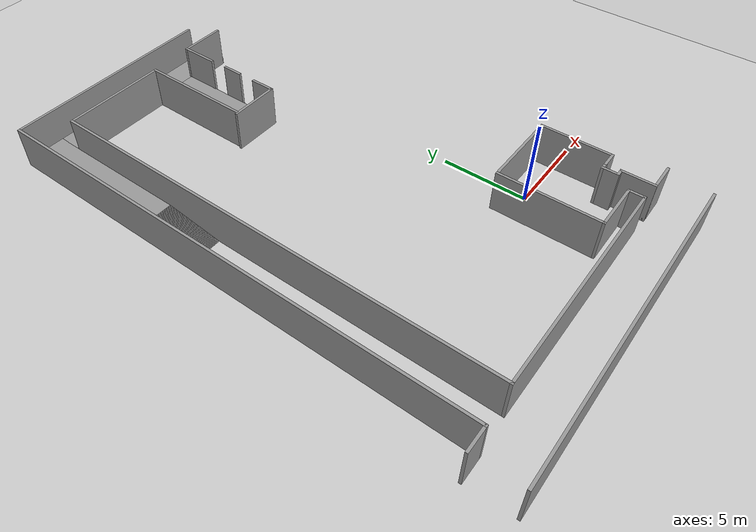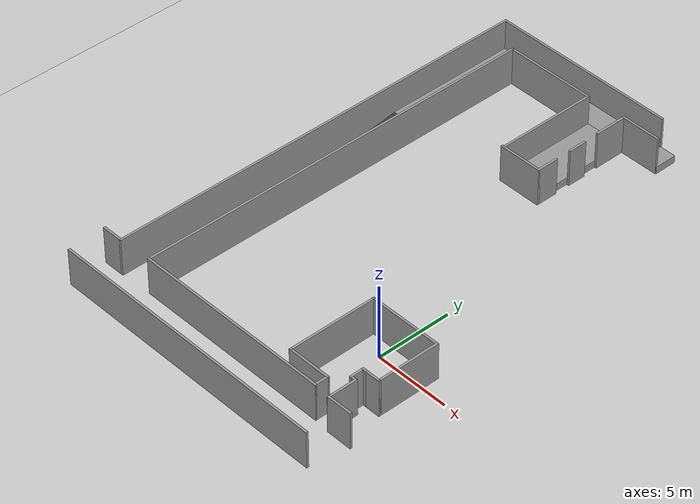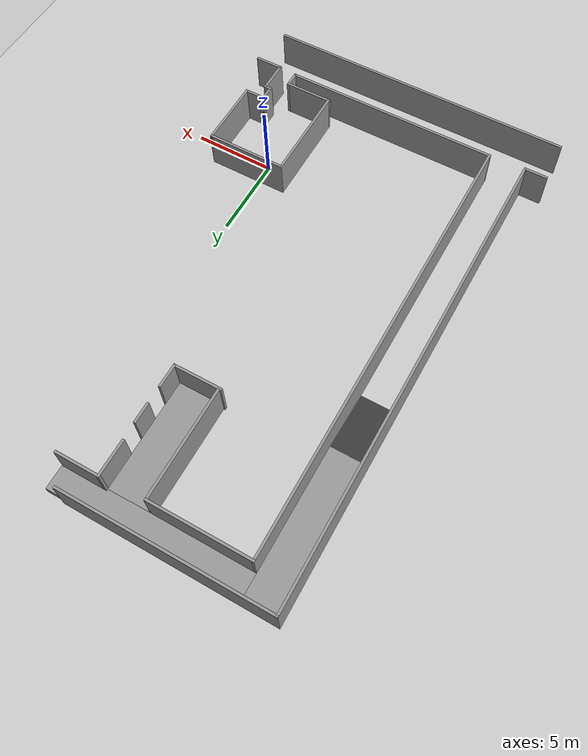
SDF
<sdf version="1.6">
 <world name="default">
  <light name="sun" type="directional">
   <pose>0 0 10 0 -0 0</pose>
   <diffuse>0.8 0.8 0.8 1</diffuse>
   <specular>0.1 0.1 0.1 1</specular>
   <attenuation>
    <range>1000</range>
    <constant>0.9</constant>
    <linear>0.01</linear>
    <quadratic>0.001</quadratic>
   </attenuation>
   <direction>-0.5 0.5 -1</direction>
  </light>
  <model name="ground_plane">
   <static>1</static>
   <link name="link">
    <collision name="collision">
     <geometry><plane><normal>0 0 1</normal><size>100 100</size></plane></geometry>
     <surface><friction><ode><mu>100</mu><mu2>50</mu2></ode></friction></surface>
    </collision>
    <visual name="visual">
     <cast_shadows>0</cast_shadows>
     <geometry><plane><normal>0 0 1</normal><size>100 100</size></plane></geometry>
     <material>
      <script><uri>file://media/materials/scripts/gazebo.material</uri><name>Gazebo/Grey</name></script>
     </material>
    </visual>
   </link>
  </model>
  <gravity>0 0 -9.8</gravity>
  <magnetic_field>6e-06 2.3e-05 -4.2e-05</magnetic_field>
  <atmosphere type="adiabatic"/>
  <physics name="default_physics" default="0" type="ode">
   <max_step_size>0.001</max_step_size>
   <real_time_factor>1</real_time_factor>
   <real_time_update_rate>1000</real_time_update_rate>
  </physics>
  <scene><ambient>0.4 0.4 0.4 1</ambient><background>0.7 0.7 0.7 1</background><shadows>1</shadows></scene>
  <spherical_coordinates>
   <surface_model>EARTH_WGS84</surface_model>
   <latitude_deg>0</latitude_deg>
   <longitude_deg>0</longitude_deg>
   <elevation>0</elevation>
   <heading_deg>0</heading_deg>
  </spherical_coordinates>
  <model name="HRI_MAP">
   <pose>-5.86756 7.56266 0 0 -0 0</pose>
   <link name="Stairs_10">
    <visual name="Stairs_10_Visual_0">
     <pose>1.21481 10.9204 0.25 0 -0 0</pose>
     <geometry><box><size>2.592 6.736 0.5</size></box></geometry>
     <material>
      <script><uri>file://media/materials/scripts/gazebo.material</uri><name>Gazebo/Grey</name></script>
      <ambient>1 1 1 1</ambient>
     </material>
    </visual>
    <collision name="Stairs_10_Collision_0">
     <geometry><box><size>2.592 6.736 0.5</size></box></geometry>
     <pose>1.21481 10.9204 0.25 0 -0 0</pose>
    </collision>
   </link>
   <link name="Stairs_2">
    <visual name="Stairs_2_Visual_0">
     <pose>-7.39374 3.33186 0.0025 0 -0 -3.14159</pose>
     <geometry><box><size>2.14498 0.035 0.005</size></box></geometry>
     <material>
      <script><uri>file://media/materials/scripts/gazebo.material</uri><name>Gazebo/Grey</name></script>
      <ambient>1 1 1 1</ambient>
     </material>
    </visual>
    <collision name="Stairs_2_Collision_0">
     <geometry><box><size>2.14498 0.035 0.005</size></box></geometry>
     <pose>-7.39374 3.33186 0.0025 0 -0 -3.14159</pose>
    </collision>
    <visual name="Stairs_2_Visual_1">
     <pose>-7.39374 3.36686 0.0075 0 -0 -3.14159</pose>
     <geometry><box><size>2.14498 0.035 0.005</size></box></geometry>
     <material>
      <script><uri>file://media/materials/scripts/gazebo.material</uri><name>Gazebo/Grey</name></script>
      <ambient>1 1 1 1</ambient>
     </material>
    </visual>
    <collision name="Stairs_2_Collision_1">
     <geometry><box><size>2.14498 0.035 0.005</size></box></geometry>
     <pose>-7.39374 3.36686 0.0075 0 -0 -3.14159</pose>
    </collision>
    <visual name="Stairs_2_Visual_2">
     <pose>-7.39374 3.40186 0.0125 0 -0 -3.14159</pose>
     <geometry><box><size>2.14498 0.035 0.005</size></box></geometry>
     <material>
      <script><uri>file://media/materials/scripts/gazebo.material</uri><name>Gazebo/Grey</name></script>
      <ambient>1 1 1 1</ambient>
     </material>
    </visual>
    <collision name="Stairs_2_Collision_2">
     <geometry><box><size>2.14498 0.035 0.005</size></box></geometry>
     <pose>-7.39374 3.40186 0.0125 0 -0 -3.14159</pose>
    </collision>
    <visual name="Stairs_2_Visual_3">
     <pose>-7.39374 3.43686 0.0175 0 -0 -3.14159</pose>
     <geometry><box><size>2.14498 0.035 0.005</size></box></geometry>
     <material>
      <script><uri>file://media/materials/scripts/gazebo.material</uri><name>Gazebo/Grey</name></script>
      <ambient>1 1 1 1</ambient>
     </material>
    </visual>
    <collision name="Stairs_2_Collision_3">
     <geometry><box><size>2.14498 0.035 0.005</size></box></geometry>
     <pose>-7.39374 3.43686 0.0175 0 -0 -3.14159</pose>
    </collision>
    <visual name="Stairs_2_Visual_4">
     <pose>-7.39374 3.47186 0.0225 0 -0 -3.14159</pose>
     <geometry><box><size>2.14498 0.035 0.005</size></box></geometry>
     <material>
      <script><uri>file://media/materials/scripts/gazebo.material</uri><name>Gazebo/Grey</name></script>
      <ambient>1 1 1 1</ambient>
     </material>
    </visual>
    <collision name="Stairs_2_Collision_4">
     <geometry><box><size>2.14498 0.035 0.005</size></box></geometry>
     <pose>-7.39374 3.47186 0.0225 0 -0 -3.14159</pose>
    </collision>
    <visual name="Stairs_2_Visual_5">
     <pose>-7.39374 3.50686 0.0275 0 -0 -3.14159</pose>
     <geometry><box><size>2.14498 0.035 0.005</size></box></geometry>
     <material>
      <script><uri>file://media/materials/scripts/gazebo.material</uri><name>Gazebo/Grey</name></script>
      <ambient>1 1 1 1</ambient>
     </material>
    </visual>
    <collision name="Stairs_2_Collision_5">
     <geometry><box><size>2.14498 0.035 0.005</size></box></geometry>
     <pose>-7.39374 3.50686 0.0275 0 -0 -3.14159</pose>
    </collision>
    <visual name="Stairs_2_Visual_6">
     <pose>-7.39374 3.54186 0.0325 0 -0 -3.14159</pose>
     <geometry><box><size>2.14498 0.035 0.005</size></box></geometry>
     <material>
      <script><uri>file://media/materials/scripts/gazebo.material</uri><name>Gazebo/Grey</name></script>
      <ambient>1 1 1 1</ambient>
     </material>
    </visual>
    <collision name="Stairs_2_Collision_6">
     <geometry><box><size>2.14498 0.035 0.005</size></box></geometry>
     <pose>-7.39374 3.54186 0.0325 0 -0 -3.14159</pose>
    </collision>
    <visual name="Stairs_2_Visual_7">
     <pose>-7.39374 3.57686 0.0375 0 -0 -3.14159</pose>
     <geometry><box><size>2.14498 0.035 0.005</size></box></geometry>
     <material>
      <script><uri>file://media/materials/scripts/gazebo.material</uri><name>Gazebo/Grey</name></script>
      <ambient>1 1 1 1</ambient>
     </material>
    </visual>
    <collision name="Stairs_2_Collision_7">
     <geometry><box><size>2.14498 0.035 0.005</size></box></geometry>
     <pose>-7.39374 3.57686 0.0375 0 -0 -3.14159</pose>
    </collision>
    <visual name="Stairs_2_Visual_8">
     <pose>-7.39374 3.61186 0.0425 0 -0 -3.14159</pose>
     <geometry><box><size>2.14498 0.035 0.005</size></box></geometry>
     <material>
      <script><uri>file://media/materials/scripts/gazebo.material</uri><name>Gazebo/Grey</name></script>
      <ambient>1 1 1 1</ambient>
     </material>
    </visual>
    <collision name="Stairs_2_Collision_8">
     <geometry><box><size>2.14498 0.035 0.005</size></box></geometry>
     <pose>-7.39374 3.61186 0.0425 0 -0 -3.14159</pose>
    </collision>
    <visual name="Stairs_2_Visual_9">
     <pose>-7.39374 3.64686 0.0475 0 -0 -3.14159</pose>
     <geometry><box><size>2.14498 0.035 0.005</size></box></geometry>
     <material>
      <script><uri>file://media/materials/scripts/gazebo.material</uri><name>Gazebo/Grey</name></script>
      <ambient>1 1 1 1</ambient>
     </material>
    </visual>
    <collision name="Stairs_2_Collision_9">
     <geometry><box><size>2.14498 0.035 0.005</size></box></geometry>
     <pose>-7.39374 3.64686 0.0475 0 -0 -3.14159</pose>
    </collision>
    <visual name="Stairs_2_Visual_10">
     <pose>-7.39374 3.68186 0.0525 0 -0 -3.14159</pose>
     <geometry><box><size>2.14498 0.035 0.005</size></box></geometry>
     <material>
      <script><uri>file://media/materials/scripts/gazebo.material</uri><name>Gazebo/Grey</name></script>
      <ambient>1 1 1 1</ambient>
     </material>
    </visual>
    <collision name="Stairs_2_Collision_10">
     <geometry><box><size>2.14498 0.035 0.005</size></box></geometry>
     <pose>-7.39374 3.68186 0.0525 0 -0 -3.14159</pose>
    </collision>
    <visual name="Stairs_2_Visual_11">
     <pose>-7.39374 3.71686 0.0575 0 -0 -3.14159</pose>
     <geometry><box><size>2.14498 0.035 0.005</size></box></geometry>
     <material>
      <script><uri>file://media/materials/scripts/gazebo.material</uri><name>Gazebo/Grey</name></script>
      <ambient>1 1 1 1</ambient>
     </material>
    </visual>
    <collision name="Stairs_2_Collision_11">
     <geometry><box><size>2.14498 0.035 0.005</size></box></geometry>
     <pose>-7.39374 3.71686 0.0575 0 -0 -3.14159</pose>
    </collision>
    <visual name="Stairs_2_Visual_12">
     <pose>-7.39374 3.75186 0.0625 0 -0 -3.14159</pose>
     <geometry><box><size>2.14498 0.035 0.005</size></box></geometry>
     <material>
      <script><uri>file://media/materials/scripts/gazebo.material</uri><name>Gazebo/Grey</name></script>
      <ambient>1 1 1 1</ambient>
     </material>
    </visual>
    <collision name="Stairs_2_Collision_12">
     <geometry><box><size>2.14498 0.035 0.005</size></box></geometry>
     <pose>-7.39374 3.75186 0.0625 0 -0 -3.14159</pose>
    </collision>
    <visual name="Stairs_2_Visual_13">
     <pose>-7.39374 3.78686 0.0675 0 -0 -3.14159</pose>
     <geometry><box><size>2.14498 0.035 0.005</size></box></geometry>
     <material>
      <script><uri>file://media/materials/scripts/gazebo.material</uri><name>Gazebo/Grey</name></script>
      <ambient>1 1 1 1</ambient>
     </material>
    </visual>
    <collision name="Stairs_2_Collision_13">
     <geometry><box><size>2.14498 0.035 0.005</size></box></geometry>
     <pose>-7.39374 3.78686 0.0675 0 -0 -3.14159</pose>
    </collision>
    <visual name="Stairs_2_Visual_14">
     <pose>-7.39374 3.82186 0.0725 0 -0 -3.14159</pose>
     <geometry><box><size>2.14498 0.035 0.005</size></box></geometry>
     <material>
      <script><uri>file://media/materials/scripts/gazebo.material</uri><name>Gazebo/Grey</name></script>
      <ambient>1 1 1 1</ambient>
     </material>
    </visual>
    <collision name="Stairs_2_Collision_14">
     <geometry><box><size>2.14498 0.035 0.005</size></box></geometry>
     <pose>-7.39374 3.82186 0.0725 0 -0 -3.14159</pose>
    </collision>
    <visual name="Stairs_2_Visual_15">
     <pose>-7.39374 3.85686 0.0775 0 -0 -3.14159</pose>
     <geometry><box><size>2.14498 0.035 0.005</size></box></geometry>
     <material>
      <script><uri>file://media/materials/scripts/gazebo.material</uri><name>Gazebo/Grey</name></script>
      <ambient>1 1 1 1</ambient>
     </material>
    </visual>
    <collision name="Stairs_2_Collision_15">
     <geometry><box><size>2.14498 0.035 0.005</size></box></geometry>
     <pose>-7.39374 3.85686 0.0775 0 -0 -3.14159</pose>
    </collision>
    <visual name="Stairs_2_Visual_16">
     <pose>-7.39374 3.89186 0.0825 0 -0 -3.14159</pose>
     <geometry><box><size>2.14498 0.035 0.005</size></box></geometry>
     <material>
      <script><uri>file://media/materials/scripts/gazebo.material</uri><name>Gazebo/Grey</name></script>
      <ambient>1 1 1 1</ambient>
     </material>
    </visual>
    <collision name="Stairs_2_Collision_16">
     <geometry><box><size>2.14498 0.035 0.005</size></box></geometry>
     <pose>-7.39374 3.89186 0.0825 0 -0 -3.14159</pose>
    </collision>
    <visual name="Stairs_2_Visual_17">
     <pose>-7.39374 3.92686 0.0875 0 -0 -3.14159</pose>
     <geometry><box><size>2.14498 0.035 0.005</size></box></geometry>
     <material>
      <script><uri>file://media/materials/scripts/gazebo.material</uri><name>Gazebo/Grey</name></script>
      <ambient>1 1 1 1</ambient>
     </material>
    </visual>
    <collision name="Stairs_2_Collision_17">
     <geometry><box><size>2.14498 0.035 0.005</size></box></geometry>
     <pose>-7.39374 3.92686 0.0875 0 -0 -3.14159</pose>
    </collision>
    <visual name="Stairs_2_Visual_18">
     <pose>-7.39374 3.96186 0.0925 0 -0 -3.14159</pose>
     <geometry><box><size>2.14498 0.035 0.005</size></box></geometry>
     <material>
      <script><uri>file://media/materials/scripts/gazebo.material</uri><name>Gazebo/Grey</name></script>
      <ambient>1 1 1 1</ambient>
     </material>
    </visual>
    <collision name="Stairs_2_Collision_18">
     <geometry><box><size>2.14498 0.035 0.005</size></box></geometry>
     <pose>-7.39374 3.96186 0.0925 0 -0 -3.14159</pose>
    </collision>
    <visual name="Stairs_2_Visual_19">
     <pose>-7.39374 3.99686 0.0975 0 -0 -3.14159</pose>
     <geometry><box><size>2.14498 0.035 0.005</size></box></geometry>
     <material>
      <script><uri>file://media/materials/scripts/gazebo.material</uri><name>Gazebo/Grey</name></script>
      <ambient>1 1 1 1</ambient>
     </material>
    </visual>
    <collision name="Stairs_2_Collision_19">
     <geometry><box><size>2.14498 0.035 0.005</size></box></geometry>
     <pose>-7.39374 3.99686 0.0975 0 -0 -3.14159</pose>
    </collision>
    <visual name="Stairs_2_Visual_20">
     <pose>-7.39374 4.03186 0.1025 0 -0 -3.14159</pose>
     <geometry><box><size>2.14498 0.035 0.005</size></box></geometry>
     <material>
      <script><uri>file://media/materials/scripts/gazebo.material</uri><name>Gazebo/Grey</name></script>
      <ambient>1 1 1 1</ambient>
     </material>
    </visual>
    <collision name="Stairs_2_Collision_20">
     <geometry><box><size>2.14498 0.035 0.005</size></box></geometry>
     <pose>-7.39374 4.03186 0.1025 0 -0 -3.14159</pose>
    </collision>
    <visual name="Stairs_2_Visual_21">
     <pose>-7.39374 4.06686 0.1075 0 -0 -3.14159</pose>
     <geometry><box><size>2.14498 0.035 0.005</size></box></geometry>
     <material>
      <script><uri>file://media/materials/scripts/gazebo.material</uri><name>Gazebo/Grey</name></script>
      <ambient>1 1 1 1</ambient>
     </material>
    </visual>
    <collision name="Stairs_2_Collision_21">
     <geometry><box><size>2.14498 0.035 0.005</size></box></geometry>
     <pose>-7.39374 4.06686 0.1075 0 -0 -3.14159</pose>
    </collision>
    <visual name="Stairs_2_Visual_22">
     <pose>-7.39374 4.10186 0.1125 0 -0 -3.14159</pose>
     <geometry><box><size>2.14498 0.035 0.005</size></box></geometry>
     <material>
      <script><uri>file://media/materials/scripts/gazebo.material</uri><name>Gazebo/Grey</name></script>
      <ambient>1 1 1 1</ambient>
     </material>
    </visual>
    <collision name="Stairs_2_Collision_22">
     <geometry><box><size>2.14498 0.035 0.005</size></box></geometry>
     <pose>-7.39374 4.10186 0.1125 0 -0 -3.14159</pose>
    </collision>
    <visual name="Stairs_2_Visual_23">
     <pose>-7.39374 4.13686 0.1175 0 -0 -3.14159</pose>
     <geometry><box><size>2.14498 0.035 0.005</size></box></geometry>
     <material>
      <script><uri>file://media/materials/scripts/gazebo.material</uri><name>Gazebo/Grey</name></script>
      <ambient>1 1 1 1</ambient>
     </material>
    </visual>
    <collision name="Stairs_2_Collision_23">
     <geometry><box><size>2.14498 0.035 0.005</size></box></geometry>
     <pose>-7.39374 4.13686 0.1175 0 -0 -3.14159</pose>
    </collision>
    <visual name="Stairs_2_Visual_24">
     <pose>-7.39374 4.17186 0.1225 0 -0 -3.14159</pose>
     <geometry><box><size>2.14498 0.035 0.005</size></box></geometry>
     <material>
      <script><uri>file://media/materials/scripts/gazebo.material</uri><name>Gazebo/Grey</name></script>
      <ambient>1 1 1 1</ambient>
     </material>
    </visual>
    <collision name="Stairs_2_Collision_24">
     <geometry><box><size>2.14498 0.035 0.005</size></box></geometry>
     <pose>-7.39374 4.17186 0.1225 0 -0 -3.14159</pose>
    </collision>
    <visual name="Stairs_2_Visual_25">
     <pose>-7.39374 4.20686 0.1275 0 -0 -3.14159</pose>
     <geometry><box><size>2.14498 0.035 0.005</size></box></geometry>
     <material>
      <script><uri>file://media/materials/scripts/gazebo.material</uri><name>Gazebo/Grey</name></script>
      <ambient>1 1 1 1</ambient>
     </material>
    </visual>
    <collision name="Stairs_2_Collision_25">
     <geometry><box><size>2.14498 0.035 0.005</size></box></geometry>
     <pose>-7.39374 4.20686 0.1275 0 -0 -3.14159</pose>
    </collision>
    <visual name="Stairs_2_Visual_26">
     <pose>-7.39374 4.24186 0.1325 0 -0 -3.14159</pose>
     <geometry><box><size>2.14498 0.035 0.005</size></box></geometry>
     <material>
      <script><uri>file://media/materials/scripts/gazebo.material</uri><name>Gazebo/Grey</name></script>
      <ambient>1 1 1 1</ambient>
     </material>
    </visual>
    <collision name="Stairs_2_Collision_26">
     <geometry><box><size>2.14498 0.035 0.005</size></box></geometry>
     <pose>-7.39374 4.24186 0.1325 0 -0 -3.14159</pose>
    </collision>
    <visual name="Stairs_2_Visual_27">
     <pose>-7.39374 4.27686 0.1375 0 -0 -3.14159</pose>
     <geometry><box><size>2.14498 0.035 0.005</size></box></geometry>
     <material>
      <script><uri>file://media/materials/scripts/gazebo.material</uri><name>Gazebo/Grey</name></script>
      <ambient>1 1 1 1</ambient>
     </material>
    </visual>
    <collision name="Stairs_2_Collision_27">
     <geometry><box><size>2.14498 0.035 0.005</size></box></geometry>
     <pose>-7.39374 4.27686 0.1375 0 -0 -3.14159</pose>
    </collision>
    <visual name="Stairs_2_Visual_28">
     <pose>-7.39374 4.31186 0.1425 0 -0 -3.14159</pose>
     <geometry><box><size>2.14498 0.035 0.005</size></box></geometry>
     <material>
      <script><uri>file://media/materials/scripts/gazebo.material</uri><name>Gazebo/Grey</name></script>
      <ambient>1 1 1 1</ambient>
     </material>
    </visual>
    <collision name="Stairs_2_Collision_28">
     <geometry><box><size>2.14498 0.035 0.005</size></box></geometry>
     <pose>-7.39374 4.31186 0.1425 0 -0 -3.14159</pose>
    </collision>
    <visual name="Stairs_2_Visual_29">
     <pose>-7.39374 4.34686 0.1475 0 -0 -3.14159</pose>
     <geometry><box><size>2.14498 0.035 0.005</size></box></geometry>
     <material>
      <script><uri>file://media/materials/scripts/gazebo.material</uri><name>Gazebo/Grey</name></script>
      <ambient>1 1 1 1</ambient>
     </material>
    </visual>
    <collision name="Stairs_2_Collision_29">
     <geometry><box><size>2.14498 0.035 0.005</size></box></geometry>
     <pose>-7.39374 4.34686 0.1475 0 -0 -3.14159</pose>
    </collision>
    <visual name="Stairs_2_Visual_30">
     <pose>-7.39374 4.38186 0.1525 0 -0 -3.14159</pose>
     <geometry><box><size>2.14498 0.035 0.005</size></box></geometry>
     <material>
      <script><uri>file://media/materials/scripts/gazebo.material</uri><name>Gazebo/Grey</name></script>
      <ambient>1 1 1 1</ambient>
     </material>
    </visual>
    <collision name="Stairs_2_Collision_30">
     <geometry><box><size>2.14498 0.035 0.005</size></box></geometry>
     <pose>-7.39374 4.38186 0.1525 0 -0 -3.14159</pose>
    </collision>
    <visual name="Stairs_2_Visual_31">
     <pose>-7.39374 4.41686 0.1575 0 -0 -3.14159</pose>
     <geometry><box><size>2.14498 0.035 0.005</size></box></geometry>
     <material>
      <script><uri>file://media/materials/scripts/gazebo.material</uri><name>Gazebo/Grey</name></script>
      <ambient>1 1 1 1</ambient>
     </material>
    </visual>
    <collision name="Stairs_2_Collision_31">
     <geometry><box><size>2.14498 0.035 0.005</size></box></geometry>
     <pose>-7.39374 4.41686 0.1575 0 -0 -3.14159</pose>
    </collision>
    <visual name="Stairs_2_Visual_32">
     <pose>-7.39374 4.45186 0.1625 0 -0 -3.14159</pose>
     <geometry><box><size>2.14498 0.035 0.005</size></box></geometry>
     <material>
      <script><uri>file://media/materials/scripts/gazebo.material</uri><name>Gazebo/Grey</name></script>
      <ambient>1 1 1 1</ambient>
     </material>
    </visual>
    <collision name="Stairs_2_Collision_32">
     <geometry><box><size>2.14498 0.035 0.005</size></box></geometry>
     <pose>-7.39374 4.45186 0.1625 0 -0 -3.14159</pose>
    </collision>
    <visual name="Stairs_2_Visual_33">
     <pose>-7.39374 4.48686 0.1675 0 -0 -3.14159</pose>
     <geometry><box><size>2.14498 0.035 0.005</size></box></geometry>
     <material>
      <script><uri>file://media/materials/scripts/gazebo.material</uri><name>Gazebo/Grey</name></script>
      <ambient>1 1 1 1</ambient>
     </material>
    </visual>
    <collision name="Stairs_2_Collision_33">
     <geometry><box><size>2.14498 0.035 0.005</size></box></geometry>
     <pose>-7.39374 4.48686 0.1675 0 -0 -3.14159</pose>
    </collision>
    <visual name="Stairs_2_Visual_34">
     <pose>-7.39374 4.52186 0.1725 0 -0 -3.14159</pose>
     <geometry><box><size>2.14498 0.035 0.005</size></box></geometry>
     <material>
      <script><uri>file://media/materials/scripts/gazebo.material</uri><name>Gazebo/Grey</name></script>
      <ambient>1 1 1 1</ambient>
     </material>
    </visual>
    <collision name="Stairs_2_Collision_34">
     <geometry><box><size>2.14498 0.035 0.005</size></box></geometry>
     <pose>-7.39374 4.52186 0.1725 0 -0 -3.14159</pose>
    </collision>
    <visual name="Stairs_2_Visual_35">
     <pose>-7.39374 4.55686 0.1775 0 -0 -3.14159</pose>
     <geometry><box><size>2.14498 0.035 0.005</size></box></geometry>
     <material>
      <script><uri>file://media/materials/scripts/gazebo.material</uri><name>Gazebo/Grey</name></script>
      <ambient>1 1 1 1</ambient>
     </material>
    </visual>
    <collision name="Stairs_2_Collision_35">
     <geometry><box><size>2.14498 0.035 0.005</size></box></geometry>
     <pose>-7.39374 4.55686 0.1775 0 -0 -3.14159</pose>
    </collision>
    <visual name="Stairs_2_Visual_36">
     <pose>-7.39374 4.59186 0.1825 0 -0 -3.14159</pose>
     <geometry><box><size>2.14498 0.035 0.005</size></box></geometry>
     <material>
      <script><uri>file://media/materials/scripts/gazebo.material</uri><name>Gazebo/Grey</name></script>
      <ambient>1 1 1 1</ambient>
     </material>
    </visual>
    <collision name="Stairs_2_Collision_36">
     <geometry><box><size>2.14498 0.035 0.005</size></box></geometry>
     <pose>-7.39374 4.59186 0.1825 0 -0 -3.14159</pose>
    </collision>
    <visual name="Stairs_2_Visual_37">
     <pose>-7.39374 4.62686 0.1875 0 -0 -3.14159</pose>
     <geometry><box><size>2.14498 0.035 0.005</size></box></geometry>
     <material>
      <script><uri>file://media/materials/scripts/gazebo.material</uri><name>Gazebo/Grey</name></script>
      <ambient>1 1 1 1</ambient>
     </material>
    </visual>
    <collision name="Stairs_2_Collision_37">
     <geometry><box><size>2.14498 0.035 0.005</size></box></geometry>
     <pose>-7.39374 4.62686 0.1875 0 -0 -3.14159</pose>
    </collision>
    <visual name="Stairs_2_Visual_38">
     <pose>-7.39374 4.66186 0.1925 0 -0 -3.14159</pose>
     <geometry><box><size>2.14498 0.035 0.005</size></box></geometry>
     <material>
      <script><uri>file://media/materials/scripts/gazebo.material</uri><name>Gazebo/Grey</name></script>
      <ambient>1 1 1 1</ambient>
     </material>
    </visual>
    <collision name="Stairs_2_Collision_38">
     <geometry><box><size>2.14498 0.035 0.005</size></box></geometry>
     <pose>-7.39374 4.66186 0.1925 0 -0 -3.14159</pose>
    </collision>
    <visual name="Stairs_2_Visual_39">
     <pose>-7.39374 4.69686 0.1975 0 -0 -3.14159</pose>
     <geometry><box><size>2.14498 0.035 0.005</size></box></geometry>
     <material>
      <script><uri>file://media/materials/scripts/gazebo.material</uri><name>Gazebo/Grey</name></script>
      <ambient>1 1 1 1</ambient>
     </material>
    </visual>
    <collision name="Stairs_2_Collision_39">
     <geometry><box><size>2.14498 0.035 0.005</size></box></geometry>
     <pose>-7.39374 4.69686 0.1975 0 -0 -3.14159</pose>
    </collision>
    <visual name="Stairs_2_Visual_40">
     <pose>-7.39374 4.73186 0.2025 0 -0 -3.14159</pose>
     <geometry><box><size>2.14498 0.035 0.005</size></box></geometry>
     <material>
      <script><uri>file://media/materials/scripts/gazebo.material</uri><name>Gazebo/Grey</name></script>
      <ambient>1 1 1 1</ambient>
     </material>
    </visual>
    <collision name="Stairs_2_Collision_40">
     <geometry><box><size>2.14498 0.035 0.005</size></box></geometry>
     <pose>-7.39374 4.73186 0.2025 0 -0 -3.14159</pose>
    </collision>
    <visual name="Stairs_2_Visual_41">
     <pose>-7.39374 4.76686 0.2075 0 -0 -3.14159</pose>
     <geometry><box><size>2.14498 0.035 0.005</size></box></geometry>
     <material>
      <script><uri>file://media/materials/scripts/gazebo.material</uri><name>Gazebo/Grey</name></script>
      <ambient>1 1 1 1</ambient>
     </material>
    </visual>
    <collision name="Stairs_2_Collision_41">
     <geometry><box><size>2.14498 0.035 0.005</size></box></geometry>
     <pose>-7.39374 4.76686 0.2075 0 -0 -3.14159</pose>
    </collision>
    <visual name="Stairs_2_Visual_42">
     <pose>-7.39374 4.80186 0.2125 0 -0 -3.14159</pose>
     <geometry><box><size>2.14498 0.035 0.005</size></box></geometry>
     <material>
      <script><uri>file://media/materials/scripts/gazebo.material</uri><name>Gazebo/Grey</name></script>
      <ambient>1 1 1 1</ambient>
     </material>
    </visual>
    <collision name="Stairs_2_Collision_42">
     <geometry><box><size>2.14498 0.035 0.005</size></box></geometry>
     <pose>-7.39374 4.80186 0.2125 0 -0 -3.14159</pose>
    </collision>
    <visual name="Stairs_2_Visual_43">
     <pose>-7.39374 4.83686 0.2175 0 -0 -3.14159</pose>
     <geometry><box><size>2.14498 0.035 0.005</size></box></geometry>
     <material>
      <script><uri>file://media/materials/scripts/gazebo.material</uri><name>Gazebo/Grey</name></script>
      <ambient>1 1 1 1</ambient>
     </material>
    </visual>
    <collision name="Stairs_2_Collision_43">
     <geometry><box><size>2.14498 0.035 0.005</size></box></geometry>
     <pose>-7.39374 4.83686 0.2175 0 -0 -3.14159</pose>
    </collision>
    <visual name="Stairs_2_Visual_44">
     <pose>-7.39374 4.87186 0.2225 0 -0 -3.14159</pose>
     <geometry><box><size>2.14498 0.035 0.005</size></box></geometry>
     <material>
      <script><uri>file://media/materials/scripts/gazebo.material</uri><name>Gazebo/Grey</name></script>
      <ambient>1 1 1 1</ambient>
     </material>
    </visual>
    <collision name="Stairs_2_Collision_44">
     <geometry><box><size>2.14498 0.035 0.005</size></box></geometry>
     <pose>-7.39374 4.87186 0.2225 0 -0 -3.14159</pose>
    </collision>
    <visual name="Stairs_2_Visual_45">
     <pose>-7.39374 4.90686 0.2275 0 -0 -3.14159</pose>
     <geometry><box><size>2.14498 0.035 0.005</size></box></geometry>
     <material>
      <script><uri>file://media/materials/scripts/gazebo.material</uri><name>Gazebo/Grey</name></script>
      <ambient>1 1 1 1</ambient>
     </material>
    </visual>
    <collision name="Stairs_2_Collision_45">
     <geometry><box><size>2.14498 0.035 0.005</size></box></geometry>
     <pose>-7.39374 4.90686 0.2275 0 -0 -3.14159</pose>
    </collision>
    <visual name="Stairs_2_Visual_46">
     <pose>-7.39374 4.94186 0.2325 0 -0 -3.14159</pose>
     <geometry><box><size>2.14498 0.035 0.005</size></box></geometry>
     <material>
      <script><uri>file://media/materials/scripts/gazebo.material</uri><name>Gazebo/Grey</name></script>
      <ambient>1 1 1 1</ambient>
     </material>
    </visual>
    <collision name="Stairs_2_Collision_46">
     <geometry><box><size>2.14498 0.035 0.005</size></box></geometry>
     <pose>-7.39374 4.94186 0.2325 0 -0 -3.14159</pose>
    </collision>
    <visual name="Stairs_2_Visual_47">
     <pose>-7.39374 4.97686 0.2375 0 -0 -3.14159</pose>
     <geometry><box><size>2.14498 0.035 0.005</size></box></geometry>
     <material>
      <script><uri>file://media/materials/scripts/gazebo.material</uri><name>Gazebo/Grey</name></script>
      <ambient>1 1 1 1</ambient>
     </material>
    </visual>
    <collision name="Stairs_2_Collision_47">
     <geometry><box><size>2.14498 0.035 0.005</size></box></geometry>
     <pose>-7.39374 4.97686 0.2375 0 -0 -3.14159</pose>
    </collision>
    <visual name="Stairs_2_Visual_48">
     <pose>-7.39374 5.01186 0.2425 0 -0 -3.14159</pose>
     <geometry><box><size>2.14498 0.035 0.005</size></box></geometry>
     <material>
      <script><uri>file://media/materials/scripts/gazebo.material</uri><name>Gazebo/Grey</name></script>
      <ambient>1 1 1 1</ambient>
     </material>
    </visual>
    <collision name="Stairs_2_Collision_48">
     <geometry><box><size>2.14498 0.035 0.005</size></box></geometry>
     <pose>-7.39374 5.01186 0.2425 0 -0 -3.14159</pose>
    </collision>
    <visual name="Stairs_2_Visual_49">
     <pose>-7.39374 5.04686 0.2475 0 -0 -3.14159</pose>
     <geometry><box><size>2.14498 0.035 0.005</size></box></geometry>
     <material>
      <script><uri>file://media/materials/scripts/gazebo.material</uri><name>Gazebo/Grey</name></script>
      <ambient>1 1 1 1</ambient>
     </material>
    </visual>
    <collision name="Stairs_2_Collision_49">
     <geometry><box><size>2.14498 0.035 0.005</size></box></geometry>
     <pose>-7.39374 5.04686 0.2475 0 -0 -3.14159</pose>
    </collision>
    <visual name="Stairs_2_Visual_50">
     <pose>-7.39374 5.08186 0.2525 0 -0 -3.14159</pose>
     <geometry><box><size>2.14498 0.035 0.005</size></box></geometry>
     <material>
      <script><uri>file://media/materials/scripts/gazebo.material</uri><name>Gazebo/Grey</name></script>
      <ambient>1 1 1 1</ambient>
     </material>
    </visual>
    <collision name="Stairs_2_Collision_50">
     <geometry><box><size>2.14498 0.035 0.005</size></box></geometry>
     <pose>-7.39374 5.08186 0.2525 0 -0 -3.14159</pose>
    </collision>
    <visual name="Stairs_2_Visual_51">
     <pose>-7.39374 5.11686 0.2575 0 -0 -3.14159</pose>
     <geometry><box><size>2.14498 0.035 0.005</size></box></geometry>
     <material>
      <script><uri>file://media/materials/scripts/gazebo.material</uri><name>Gazebo/Grey</name></script>
      <ambient>1 1 1 1</ambient>
     </material>
    </visual>
    <collision name="Stairs_2_Collision_51">
     <geometry><box><size>2.14498 0.035 0.005</size></box></geometry>
     <pose>-7.39374 5.11686 0.2575 0 -0 -3.14159</pose>
    </collision>
    <visual name="Stairs_2_Visual_52">
     <pose>-7.39374 5.15186 0.2625 0 -0 -3.14159</pose>
     <geometry><box><size>2.14498 0.035 0.005</size></box></geometry>
     <material>
      <script><uri>file://media/materials/scripts/gazebo.material</uri><name>Gazebo/Grey</name></script>
      <ambient>1 1 1 1</ambient>
     </material>
    </visual>
    <collision name="Stairs_2_Collision_52">
     <geometry><box><size>2.14498 0.035 0.005</size></box></geometry>
     <pose>-7.39374 5.15186 0.2625 0 -0 -3.14159</pose>
    </collision>
    <visual name="Stairs_2_Visual_53">
     <pose>-7.39374 5.18686 0.2675 0 -0 -3.14159</pose>
     <geometry><box><size>2.14498 0.035 0.005</size></box></geometry>
     <material>
      <script><uri>file://media/materials/scripts/gazebo.material</uri><name>Gazebo/Grey</name></script>
      <ambient>1 1 1 1</ambient>
     </material>
    </visual>
    <collision name="Stairs_2_Collision_53">
     <geometry><box><size>2.14498 0.035 0.005</size></box></geometry>
     <pose>-7.39374 5.18686 0.2675 0 -0 -3.14159</pose>
    </collision>
    <visual name="Stairs_2_Visual_54">
     <pose>-7.39374 5.22186 0.2725 0 -0 -3.14159</pose>
     <geometry><box><size>2.14498 0.035 0.005</size></box></geometry>
     <material>
      <script><uri>file://media/materials/scripts/gazebo.material</uri><name>Gazebo/Grey</name></script>
      <ambient>1 1 1 1</ambient>
     </material>
    </visual>
    <collision name="Stairs_2_Collision_54">
     <geometry><box><size>2.14498 0.035 0.005</size></box></geometry>
     <pose>-7.39374 5.22186 0.2725 0 -0 -3.14159</pose>
    </collision>
    <visual name="Stairs_2_Visual_55">
     <pose>-7.39374 5.25686 0.2775 0 -0 -3.14159</pose>
     <geometry><box><size>2.14498 0.035 0.005</size></box></geometry>
     <material>
      <script><uri>file://media/materials/scripts/gazebo.material</uri><name>Gazebo/Grey</name></script>
      <ambient>1 1 1 1</ambient>
     </material>
    </visual>
    <collision name="Stairs_2_Collision_55">
     <geometry><box><size>2.14498 0.035 0.005</size></box></geometry>
     <pose>-7.39374 5.25686 0.2775 0 -0 -3.14159</pose>
    </collision>
    <visual name="Stairs_2_Visual_56">
     <pose>-7.39374 5.29186 0.2825 0 -0 -3.14159</pose>
     <geometry><box><size>2.14498 0.035 0.005</size></box></geometry>
     <material>
      <script><uri>file://media/materials/scripts/gazebo.material</uri><name>Gazebo/Grey</name></script>
      <ambient>1 1 1 1</ambient>
     </material>
    </visual>
    <collision name="Stairs_2_Collision_56">
     <geometry><box><size>2.14498 0.035 0.005</size></box></geometry>
     <pose>-7.39374 5.29186 0.2825 0 -0 -3.14159</pose>
    </collision>
    <visual name="Stairs_2_Visual_57">
     <pose>-7.39374 5.32686 0.2875 0 -0 -3.14159</pose>
     <geometry><box><size>2.14498 0.035 0.005</size></box></geometry>
     <material>
      <script><uri>file://media/materials/scripts/gazebo.material</uri><name>Gazebo/Grey</name></script>
      <ambient>1 1 1 1</ambient>
     </material>
    </visual>
    <collision name="Stairs_2_Collision_57">
     <geometry><box><size>2.14498 0.035 0.005</size></box></geometry>
     <pose>-7.39374 5.32686 0.2875 0 -0 -3.14159</pose>
    </collision>
    <visual name="Stairs_2_Visual_58">
     <pose>-7.39374 5.36186 0.2925 0 -0 -3.14159</pose>
     <geometry><box><size>2.14498 0.035 0.005</size></box></geometry>
     <material>
      <script><uri>file://media/materials/scripts/gazebo.material</uri><name>Gazebo/Grey</name></script>
      <ambient>1 1 1 1</ambient>
     </material>
    </visual>
    <collision name="Stairs_2_Collision_58">
     <geometry><box><size>2.14498 0.035 0.005</size></box></geometry>
     <pose>-7.39374 5.36186 0.2925 0 -0 -3.14159</pose>
    </collision>
    <visual name="Stairs_2_Visual_59">
     <pose>-7.39374 5.39686 0.2975 0 -0 -3.14159</pose>
     <geometry><box><size>2.14498 0.035 0.005</size></box></geometry>
     <material>
      <script><uri>file://media/materials/scripts/gazebo.material</uri><name>Gazebo/Grey</name></script>
      <ambient>1 1 1 1</ambient>
     </material>
    </visual>
    <collision name="Stairs_2_Collision_59">
     <geometry><box><size>2.14498 0.035 0.005</size></box></geometry>
     <pose>-7.39374 5.39686 0.2975 0 -0 -3.14159</pose>
    </collision>
    <visual name="Stairs_2_Visual_60">
     <pose>-7.39374 5.43186 0.3025 0 -0 -3.14159</pose>
     <geometry><box><size>2.14498 0.035 0.005</size></box></geometry>
     <material>
      <script><uri>file://media/materials/scripts/gazebo.material</uri><name>Gazebo/Grey</name></script>
      <ambient>1 1 1 1</ambient>
     </material>
    </visual>
    <collision name="Stairs_2_Collision_60">
     <geometry><box><size>2.14498 0.035 0.005</size></box></geometry>
     <pose>-7.39374 5.43186 0.3025 0 -0 -3.14159</pose>
    </collision>
    <visual name="Stairs_2_Visual_61">
     <pose>-7.39374 5.46686 0.3075 0 -0 -3.14159</pose>
     <geometry><box><size>2.14498 0.035 0.005</size></box></geometry>
     <material>
      <script><uri>file://media/materials/scripts/gazebo.material</uri><name>Gazebo/Grey</name></script>
      <ambient>1 1 1 1</ambient>
     </material>
    </visual>
    <collision name="Stairs_2_Collision_61">
     <geometry><box><size>2.14498 0.035 0.005</size></box></geometry>
     <pose>-7.39374 5.46686 0.3075 0 -0 -3.14159</pose>
    </collision>
    <visual name="Stairs_2_Visual_62">
     <pose>-7.39374 5.50186 0.3125 0 -0 -3.14159</pose>
     <geometry><box><size>2.14498 0.035 0.005</size></box></geometry>
     <material>
      <script><uri>file://media/materials/scripts/gazebo.material</uri><name>Gazebo/Grey</name></script>
      <ambient>1 1 1 1</ambient>
     </material>
    </visual>
    <collision name="Stairs_2_Collision_62">
     <geometry><box><size>2.14498 0.035 0.005</size></box></geometry>
     <pose>-7.39374 5.50186 0.3125 0 -0 -3.14159</pose>
    </collision>
    <visual name="Stairs_2_Visual_63">
     <pose>-7.39374 5.53686 0.3175 0 -0 -3.14159</pose>
     <geometry><box><size>2.14498 0.035 0.005</size></box></geometry>
     <material>
      <script><uri>file://media/materials/scripts/gazebo.material</uri><name>Gazebo/Grey</name></script>
      <ambient>1 1 1 1</ambient>
     </material>
    </visual>
    <collision name="Stairs_2_Collision_63">
     <geometry><box><size>2.14498 0.035 0.005</size></box></geometry>
     <pose>-7.39374 5.53686 0.3175 0 -0 -3.14159</pose>
    </collision>
    <visual name="Stairs_2_Visual_64">
     <pose>-7.39374 5.57186 0.3225 0 -0 -3.14159</pose>
     <geometry><box><size>2.14498 0.035 0.005</size></box></geometry>
     <material>
      <script><uri>file://media/materials/scripts/gazebo.material</uri><name>Gazebo/Grey</name></script>
      <ambient>1 1 1 1</ambient>
     </material>
    </visual>
    <collision name="Stairs_2_Collision_64">
     <geometry><box><size>2.14498 0.035 0.005</size></box></geometry>
     <pose>-7.39374 5.57186 0.3225 0 -0 -3.14159</pose>
    </collision>
    <visual name="Stairs_2_Visual_65">
     <pose>-7.39374 5.60686 0.3275 0 -0 -3.14159</pose>
     <geometry><box><size>2.14498 0.035 0.005</size></box></geometry>
     <material>
      <script><uri>file://media/materials/scripts/gazebo.material</uri><name>Gazebo/Grey</name></script>
      <ambient>1 1 1 1</ambient>
     </material>
    </visual>
    <collision name="Stairs_2_Collision_65">
     <geometry><box><size>2.14498 0.035 0.005</size></box></geometry>
     <pose>-7.39374 5.60686 0.3275 0 -0 -3.14159</pose>
    </collision>
    <visual name="Stairs_2_Visual_66">
     <pose>-7.39374 5.64186 0.3325 0 -0 -3.14159</pose>
     <geometry><box><size>2.14498 0.035 0.005</size></box></geometry>
     <material>
      <script><uri>file://media/materials/scripts/gazebo.material</uri><name>Gazebo/Grey</name></script>
      <ambient>1 1 1 1</ambient>
     </material>
    </visual>
    <collision name="Stairs_2_Collision_66">
     <geometry><box><size>2.14498 0.035 0.005</size></box></geometry>
     <pose>-7.39374 5.64186 0.3325 0 -0 -3.14159</pose>
    </collision>
    <visual name="Stairs_2_Visual_67">
     <pose>-7.39374 5.67686 0.3375 0 -0 -3.14159</pose>
     <geometry><box><size>2.14498 0.035 0.005</size></box></geometry>
     <material>
      <script><uri>file://media/materials/scripts/gazebo.material</uri><name>Gazebo/Grey</name></script>
      <ambient>1 1 1 1</ambient>
     </material>
    </visual>
    <collision name="Stairs_2_Collision_67">
     <geometry><box><size>2.14498 0.035 0.005</size></box></geometry>
     <pose>-7.39374 5.67686 0.3375 0 -0 -3.14159</pose>
    </collision>
    <visual name="Stairs_2_Visual_68">
     <pose>-7.39374 5.71186 0.3425 0 -0 -3.14159</pose>
     <geometry><box><size>2.14498 0.035 0.005</size></box></geometry>
     <material>
      <script><uri>file://media/materials/scripts/gazebo.material</uri><name>Gazebo/Grey</name></script>
      <ambient>1 1 1 1</ambient>
     </material>
    </visual>
    <collision name="Stairs_2_Collision_68">
     <geometry><box><size>2.14498 0.035 0.005</size></box></geometry>
     <pose>-7.39374 5.71186 0.3425 0 -0 -3.14159</pose>
    </collision>
    <visual name="Stairs_2_Visual_69">
     <pose>-7.39374 5.74686 0.3475 0 -0 -3.14159</pose>
     <geometry><box><size>2.14498 0.035 0.005</size></box></geometry>
     <material>
      <script><uri>file://media/materials/scripts/gazebo.material</uri><name>Gazebo/Grey</name></script>
      <ambient>1 1 1 1</ambient>
     </material>
    </visual>
    <collision name="Stairs_2_Collision_69">
     <geometry><box><size>2.14498 0.035 0.005</size></box></geometry>
     <pose>-7.39374 5.74686 0.3475 0 -0 -3.14159</pose>
    </collision>
    <visual name="Stairs_2_Visual_70">
     <pose>-7.39374 5.78186 0.3525 0 -0 -3.14159</pose>
     <geometry><box><size>2.14498 0.035 0.005</size></box></geometry>
     <material>
      <script><uri>file://media/materials/scripts/gazebo.material</uri><name>Gazebo/Grey</name></script>
      <ambient>1 1 1 1</ambient>
     </material>
    </visual>
    <collision name="Stairs_2_Collision_70">
     <geometry><box><size>2.14498 0.035 0.005</size></box></geometry>
     <pose>-7.39374 5.78186 0.3525 0 -0 -3.14159</pose>
    </collision>
    <visual name="Stairs_2_Visual_71">
     <pose>-7.39374 5.81686 0.3575 0 -0 -3.14159</pose>
     <geometry><box><size>2.14498 0.035 0.005</size></box></geometry>
     <material>
      <script><uri>file://media/materials/scripts/gazebo.material</uri><name>Gazebo/Grey</name></script>
      <ambient>1 1 1 1</ambient>
     </material>
    </visual>
    <collision name="Stairs_2_Collision_71">
     <geometry><box><size>2.14498 0.035 0.005</size></box></geometry>
     <pose>-7.39374 5.81686 0.3575 0 -0 -3.14159</pose>
    </collision>
    <visual name="Stairs_2_Visual_72">
     <pose>-7.39374 5.85186 0.3625 0 -0 -3.14159</pose>
     <geometry><box><size>2.14498 0.035 0.005</size></box></geometry>
     <material>
      <script><uri>file://media/materials/scripts/gazebo.material</uri><name>Gazebo/Grey</name></script>
      <ambient>1 1 1 1</ambient>
     </material>
    </visual>
    <collision name="Stairs_2_Collision_72">
     <geometry><box><size>2.14498 0.035 0.005</size></box></geometry>
     <pose>-7.39374 5.85186 0.3625 0 -0 -3.14159</pose>
    </collision>
    <visual name="Stairs_2_Visual_73">
     <pose>-7.39374 5.88686 0.3675 0 -0 -3.14159</pose>
     <geometry><box><size>2.14498 0.035 0.005</size></box></geometry>
     <material>
      <script><uri>file://media/materials/scripts/gazebo.material</uri><name>Gazebo/Grey</name></script>
      <ambient>1 1 1 1</ambient>
     </material>
    </visual>
    <collision name="Stairs_2_Collision_73">
     <geometry><box><size>2.14498 0.035 0.005</size></box></geometry>
     <pose>-7.39374 5.88686 0.3675 0 -0 -3.14159</pose>
    </collision>
    <visual name="Stairs_2_Visual_74">
     <pose>-7.39374 5.92186 0.3725 0 -0 -3.14159</pose>
     <geometry><box><size>2.14498 0.035 0.005</size></box></geometry>
     <material>
      <script><uri>file://media/materials/scripts/gazebo.material</uri><name>Gazebo/Grey</name></script>
      <ambient>1 1 1 1</ambient>
     </material>
    </visual>
    <collision name="Stairs_2_Collision_74">
     <geometry><box><size>2.14498 0.035 0.005</size></box></geometry>
     <pose>-7.39374 5.92186 0.3725 0 -0 -3.14159</pose>
    </collision>
    <visual name="Stairs_2_Visual_75">
     <pose>-7.39374 5.95686 0.3775 0 -0 -3.14159</pose>
     <geometry><box><size>2.14498 0.035 0.005</size></box></geometry>
     <material>
      <script><uri>file://media/materials/scripts/gazebo.material</uri><name>Gazebo/Grey</name></script>
      <ambient>1 1 1 1</ambient>
     </material>
    </visual>
    <collision name="Stairs_2_Collision_75">
     <geometry><box><size>2.14498 0.035 0.005</size></box></geometry>
     <pose>-7.39374 5.95686 0.3775 0 -0 -3.14159</pose>
    </collision>
    <visual name="Stairs_2_Visual_76">
     <pose>-7.39374 5.99186 0.3825 0 -0 -3.14159</pose>
     <geometry><box><size>2.14498 0.035 0.005</size></box></geometry>
     <material>
      <script><uri>file://media/materials/scripts/gazebo.material</uri><name>Gazebo/Grey</name></script>
      <ambient>1 1 1 1</ambient>
     </material>
    </visual>
    <collision name="Stairs_2_Collision_76">
     <geometry><box><size>2.14498 0.035 0.005</size></box></geometry>
     <pose>-7.39374 5.99186 0.3825 0 -0 -3.14159</pose>
    </collision>
    <visual name="Stairs_2_Visual_77">
     <pose>-7.39374 6.02686 0.3875 0 -0 -3.14159</pose>
     <geometry><box><size>2.14498 0.035 0.005</size></box></geometry>
     <material>
      <script><uri>file://media/materials/scripts/gazebo.material</uri><name>Gazebo/Grey</name></script>
      <ambient>1 1 1 1</ambient>
     </material>
    </visual>
    <collision name="Stairs_2_Collision_77">
     <geometry><box><size>2.14498 0.035 0.005</size></box></geometry>
     <pose>-7.39374 6.02686 0.3875 0 -0 -3.14159</pose>
    </collision>
    <visual name="Stairs_2_Visual_78">
     <pose>-7.39374 6.06186 0.3925 0 -0 -3.14159</pose>
     <geometry><box><size>2.14498 0.035 0.005</size></box></geometry>
     <material>
      <script><uri>file://media/materials/scripts/gazebo.material</uri><name>Gazebo/Grey</name></script>
      <ambient>1 1 1 1</ambient>
     </material>
    </visual>
    <collision name="Stairs_2_Collision_78">
     <geometry><box><size>2.14498 0.035 0.005</size></box></geometry>
     <pose>-7.39374 6.06186 0.3925 0 -0 -3.14159</pose>
    </collision>
    <visual name="Stairs_2_Visual_79">
     <pose>-7.39374 6.09686 0.3975 0 -0 -3.14159</pose>
     <geometry><box><size>2.14498 0.035 0.005</size></box></geometry>
     <material>
      <script><uri>file://media/materials/scripts/gazebo.material</uri><name>Gazebo/Grey</name></script>
      <ambient>1 1 1 1</ambient>
     </material>
    </visual>
    <collision name="Stairs_2_Collision_79">
     <geometry><box><size>2.14498 0.035 0.005</size></box></geometry>
     <pose>-7.39374 6.09686 0.3975 0 -0 -3.14159</pose>
    </collision>
    <visual name="Stairs_2_Visual_80">
     <pose>-7.39374 6.13186 0.4025 0 -0 -3.14159</pose>
     <geometry><box><size>2.14498 0.035 0.005</size></box></geometry>
     <material>
      <script><uri>file://media/materials/scripts/gazebo.material</uri><name>Gazebo/Grey</name></script>
      <ambient>1 1 1 1</ambient>
     </material>
    </visual>
    <collision name="Stairs_2_Collision_80">
     <geometry><box><size>2.14498 0.035 0.005</size></box></geometry>
     <pose>-7.39374 6.13186 0.4025 0 -0 -3.14159</pose>
    </collision>
    <visual name="Stairs_2_Visual_81">
     <pose>-7.39374 6.16686 0.4075 0 -0 -3.14159</pose>
     <geometry><box><size>2.14498 0.035 0.005</size></box></geometry>
     <material>
      <script><uri>file://media/materials/scripts/gazebo.material</uri><name>Gazebo/Grey</name></script>
      <ambient>1 1 1 1</ambient>
     </material>
    </visual>
    <collision name="Stairs_2_Collision_81">
     <geometry><box><size>2.14498 0.035 0.005</size></box></geometry>
     <pose>-7.39374 6.16686 0.4075 0 -0 -3.14159</pose>
    </collision>
    <visual name="Stairs_2_Visual_82">
     <pose>-7.39374 6.20186 0.4125 0 -0 -3.14159</pose>
     <geometry><box><size>2.14498 0.035 0.005</size></box></geometry>
     <material>
      <script><uri>file://media/materials/scripts/gazebo.material</uri><name>Gazebo/Grey</name></script>
      <ambient>1 1 1 1</ambient>
     </material>
    </visual>
    <collision name="Stairs_2_Collision_82">
     <geometry><box><size>2.14498 0.035 0.005</size></box></geometry>
     <pose>-7.39374 6.20186 0.4125 0 -0 -3.14159</pose>
    </collision>
    <visual name="Stairs_2_Visual_83">
     <pose>-7.39374 6.23686 0.4175 0 -0 -3.14159</pose>
     <geometry><box><size>2.14498 0.035 0.005</size></box></geometry>
     <material>
      <script><uri>file://media/materials/scripts/gazebo.material</uri><name>Gazebo/Grey</name></script>
      <ambient>1 1 1 1</ambient>
     </material>
    </visual>
    <collision name="Stairs_2_Collision_83">
     <geometry><box><size>2.14498 0.035 0.005</size></box></geometry>
     <pose>-7.39374 6.23686 0.4175 0 -0 -3.14159</pose>
    </collision>
    <visual name="Stairs_2_Visual_84">
     <pose>-7.39374 6.27186 0.4225 0 -0 -3.14159</pose>
     <geometry><box><size>2.14498 0.035 0.005</size></box></geometry>
     <material>
      <script><uri>file://media/materials/scripts/gazebo.material</uri><name>Gazebo/Grey</name></script>
      <ambient>1 1 1 1</ambient>
     </material>
    </visual>
    <collision name="Stairs_2_Collision_84">
     <geometry><box><size>2.14498 0.035 0.005</size></box></geometry>
     <pose>-7.39374 6.27186 0.4225 0 -0 -3.14159</pose>
    </collision>
    <visual name="Stairs_2_Visual_85">
     <pose>-7.39374 6.30686 0.4275 0 -0 -3.14159</pose>
     <geometry><box><size>2.14498 0.035 0.005</size></box></geometry>
     <material>
      <script><uri>file://media/materials/scripts/gazebo.material</uri><name>Gazebo/Grey</name></script>
      <ambient>1 1 1 1</ambient>
     </material>
    </visual>
    <collision name="Stairs_2_Collision_85">
     <geometry><box><size>2.14498 0.035 0.005</size></box></geometry>
     <pose>-7.39374 6.30686 0.4275 0 -0 -3.14159</pose>
    </collision>
    <visual name="Stairs_2_Visual_86">
     <pose>-7.39374 6.34186 0.4325 0 -0 -3.14159</pose>
     <geometry><box><size>2.14498 0.035 0.005</size></box></geometry>
     <material>
      <script><uri>file://media/materials/scripts/gazebo.material</uri><name>Gazebo/Grey</name></script>
      <ambient>1 1 1 1</ambient>
     </material>
    </visual>
    <collision name="Stairs_2_Collision_86">
     <geometry><box><size>2.14498 0.035 0.005</size></box></geometry>
     <pose>-7.39374 6.34186 0.4325 0 -0 -3.14159</pose>
    </collision>
    <visual name="Stairs_2_Visual_87">
     <pose>-7.39374 6.37686 0.4375 0 -0 -3.14159</pose>
     <geometry><box><size>2.14498 0.035 0.005</size></box></geometry>
     <material>
      <script><uri>file://media/materials/scripts/gazebo.material</uri><name>Gazebo/Grey</name></script>
      <ambient>1 1 1 1</ambient>
     </material>
    </visual>
    <collision name="Stairs_2_Collision_87">
     <geometry><box><size>2.14498 0.035 0.005</size></box></geometry>
     <pose>-7.39374 6.37686 0.4375 0 -0 -3.14159</pose>
    </collision>
    <visual name="Stairs_2_Visual_88">
     <pose>-7.39374 6.41186 0.4425 0 -0 -3.14159</pose>
     <geometry><box><size>2.14498 0.035 0.005</size></box></geometry>
     <material>
      <script><uri>file://media/materials/scripts/gazebo.material</uri><name>Gazebo/Grey</name></script>
      <ambient>1 1 1 1</ambient>
     </material>
    </visual>
    <collision name="Stairs_2_Collision_88">
     <geometry><box><size>2.14498 0.035 0.005</size></box></geometry>
     <pose>-7.39374 6.41186 0.4425 0 -0 -3.14159</pose>
    </collision>
    <visual name="Stairs_2_Visual_89">
     <pose>-7.39374 6.44686 0.4475 0 -0 -3.14159</pose>
     <geometry><box><size>2.14498 0.035 0.005</size></box></geometry>
     <material>
      <script><uri>file://media/materials/scripts/gazebo.material</uri><name>Gazebo/Grey</name></script>
      <ambient>1 1 1 1</ambient>
     </material>
    </visual>
    <collision name="Stairs_2_Collision_89">
     <geometry><box><size>2.14498 0.035 0.005</size></box></geometry>
     <pose>-7.39374 6.44686 0.4475 0 -0 -3.14159</pose>
    </collision>
    <visual name="Stairs_2_Visual_90">
     <pose>-7.39374 6.48186 0.4525 0 -0 -3.14159</pose>
     <geometry><box><size>2.14498 0.035 0.005</size></box></geometry>
     <material>
      <script><uri>file://media/materials/scripts/gazebo.material</uri><name>Gazebo/Grey</name></script>
      <ambient>1 1 1 1</ambient>
     </material>
    </visual>
    <collision name="Stairs_2_Collision_90">
     <geometry><box><size>2.14498 0.035 0.005</size></box></geometry>
     <pose>-7.39374 6.48186 0.4525 0 -0 -3.14159</pose>
    </collision>
    <visual name="Stairs_2_Visual_91">
     <pose>-7.39374 6.51686 0.4575 0 -0 -3.14159</pose>
     <geometry><box><size>2.14498 0.035 0.005</size></box></geometry>
     <material>
      <script><uri>file://media/materials/scripts/gazebo.material</uri><name>Gazebo/Grey</name></script>
      <ambient>1 1 1 1</ambient>
     </material>
    </visual>
    <collision name="Stairs_2_Collision_91">
     <geometry><box><size>2.14498 0.035 0.005</size></box></geometry>
     <pose>-7.39374 6.51686 0.4575 0 -0 -3.14159</pose>
    </collision>
    <visual name="Stairs_2_Visual_92">
     <pose>-7.39374 6.55186 0.4625 0 -0 -3.14159</pose>
     <geometry><box><size>2.14498 0.035 0.005</size></box></geometry>
     <material>
      <script><uri>file://media/materials/scripts/gazebo.material</uri><name>Gazebo/Grey</name></script>
      <ambient>1 1 1 1</ambient>
     </material>
    </visual>
    <collision name="Stairs_2_Collision_92">
     <geometry><box><size>2.14498 0.035 0.005</size></box></geometry>
     <pose>-7.39374 6.55186 0.4625 0 -0 -3.14159</pose>
    </collision>
    <visual name="Stairs_2_Visual_93">
     <pose>-7.39374 6.58686 0.4675 0 -0 -3.14159</pose>
     <geometry><box><size>2.14498 0.035 0.005</size></box></geometry>
     <material>
      <script><uri>file://media/materials/scripts/gazebo.material</uri><name>Gazebo/Grey</name></script>
      <ambient>1 1 1 1</ambient>
     </material>
    </visual>
    <collision name="Stairs_2_Collision_93">
     <geometry><box><size>2.14498 0.035 0.005</size></box></geometry>
     <pose>-7.39374 6.58686 0.4675 0 -0 -3.14159</pose>
    </collision>
    <visual name="Stairs_2_Visual_94">
     <pose>-7.39374 6.62186 0.4725 0 -0 -3.14159</pose>
     <geometry><box><size>2.14498 0.035 0.005</size></box></geometry>
     <material>
      <script><uri>file://media/materials/scripts/gazebo.material</uri><name>Gazebo/Grey</name></script>
      <ambient>1 1 1 1</ambient>
     </material>
    </visual>
    <collision name="Stairs_2_Collision_94">
     <geometry><box><size>2.14498 0.035 0.005</size></box></geometry>
     <pose>-7.39374 6.62186 0.4725 0 -0 -3.14159</pose>
    </collision>
    <visual name="Stairs_2_Visual_95">
     <pose>-7.39374 6.65686 0.4775 0 -0 -3.14159</pose>
     <geometry><box><size>2.14498 0.035 0.005</size></box></geometry>
     <material>
      <script><uri>file://media/materials/scripts/gazebo.material</uri><name>Gazebo/Grey</name></script>
      <ambient>1 1 1 1</ambient>
     </material>
    </visual>
    <collision name="Stairs_2_Collision_95">
     <geometry><box><size>2.14498 0.035 0.005</size></box></geometry>
     <pose>-7.39374 6.65686 0.4775 0 -0 -3.14159</pose>
    </collision>
    <visual name="Stairs_2_Visual_96">
     <pose>-7.39374 6.69186 0.4825 0 -0 -3.14159</pose>
     <geometry><box><size>2.14498 0.035 0.005</size></box></geometry>
     <material>
      <script><uri>file://media/materials/scripts/gazebo.material</uri><name>Gazebo/Grey</name></script>
      <ambient>1 1 1 1</ambient>
     </material>
    </visual>
    <collision name="Stairs_2_Collision_96">
     <geometry><box><size>2.14498 0.035 0.005</size></box></geometry>
     <pose>-7.39374 6.69186 0.4825 0 -0 -3.14159</pose>
    </collision>
    <visual name="Stairs_2_Visual_97">
     <pose>-7.39374 6.72686 0.4875 0 -0 -3.14159</pose>
     <geometry><box><size>2.14498 0.035 0.005</size></box></geometry>
     <material>
      <script><uri>file://media/materials/scripts/gazebo.material</uri><name>Gazebo/Grey</name></script>
      <ambient>1 1 1 1</ambient>
     </material>
    </visual>
    <collision name="Stairs_2_Collision_97">
     <geometry><box><size>2.14498 0.035 0.005</size></box></geometry>
     <pose>-7.39374 6.72686 0.4875 0 -0 -3.14159</pose>
    </collision>
    <visual name="Stairs_2_Visual_98">
     <pose>-7.39374 6.76186 0.4925 0 -0 -3.14159</pose>
     <geometry><box><size>2.14498 0.035 0.005</size></box></geometry>
     <material>
      <script><uri>file://media/materials/scripts/gazebo.material</uri><name>Gazebo/Grey</name></script>
      <ambient>1 1 1 1</ambient>
     </material>
    </visual>
    <collision name="Stairs_2_Collision_98">
     <geometry><box><size>2.14498 0.035 0.005</size></box></geometry>
     <pose>-7.39374 6.76186 0.4925 0 -0 -3.14159</pose>
    </collision>
    <visual name="Stairs_2_Visual_99">
     <pose>-7.39374 6.79686 0.4975 0 -0 -3.14159</pose>
     <geometry><box><size>2.14498 0.035 0.005</size></box></geometry>
     <material>
      <script><uri>file://media/materials/scripts/gazebo.material</uri><name>Gazebo/Grey</name></script>
      <ambient>1 1 1 1</ambient>
     </material>
    </visual>
    <collision name="Stairs_2_Collision_99">
     <geometry><box><size>2.14498 0.035 0.005</size></box></geometry>
     <pose>-7.39374 6.79686 0.4975 0 -0 -3.14159</pose>
    </collision>
   </link>
   <link name="Stairs_6">
    <visual name="Stairs_6_Visual_0">
     <pose>-7.41654 11.2877 0.25 0 -0 0</pose>
     <geometry><box><size>2.21745 8.93941 0.5</size></box></geometry>
     <material>
      <script><uri>file://media/materials/scripts/gazebo.material</uri><name>Gazebo/Grey</name></script>
      <ambient>1 1 1 1</ambient>
     </material>
    </visual>
    <collision name="Stairs_6_Collision_0">
     <geometry><box><size>2.21745 8.93941 0.5</size></box></geometry>
     <pose>-7.41654 11.2877 0.25 0 -0 0</pose>
    </collision>
   </link>
   <link name="Stairs_8">
    <visual name="Stairs_8_Visual_0">
     <pose>-0.516707 15.0306 0.25 0 -0 0</pose>
     <geometry><box><size>11.616 1.524 0.5</size></box></geometry>
     <material>
      <script><uri>file://media/materials/scripts/gazebo.material</uri><name>Gazebo/Grey</name></script>
      <ambient>1 1 1 1</ambient>
     </material>
    </visual>
    <collision name="Stairs_8_Collision_0">
     <geometry><box><size>11.616 1.524 0.5</size></box></geometry>
     <pose>-0.516707 15.0306 0.25 0 -0 0</pose>
    </collision>
   </link>
   <link name="Wall_1">
    <collision name="Wall_1_Collision">
     <geometry><box><size>1 0.15 2.5</size></box></geometry>
     <pose>0 0 1.25 0 -0 0</pose>
    </collision>
    <visual name="Wall_1_Visual">
     <pose>0 0 1.25 0 -0 0</pose>
     <geometry><box><size>1 0.15 2.5</size></box></geometry>
     <material>
      <script><uri>file://media/materials/scripts/gazebo.material</uri><name>Gazebo/Grey</name></script>
      <ambient>1 1 1 1</ambient>
     </material>
    </visual>
    <pose>7.09624 -12.7378 0 0 0 -1.5708</pose>
   </link>
   <link name="Wall_10">
    <collision name="Wall_10_Collision">
     <geometry><box><size>0.5 0.15 2.5</size></box></geometry>
     <pose>0 0 1.25 0 -0 0</pose>
    </collision>
    <visual name="Wall_10_Visual">
     <pose>0 0 1.25 0 -0 0</pose>
     <geometry><box><size>0.5 0.15 2.5</size></box></geometry>
     <material>
      <script><uri>file://media/materials/scripts/gazebo.material</uri><name>Gazebo/Grey</name></script>
      <ambient>1 1 1 1</ambient>
     </material>
    </visual>
    <pose>8.07124 -11.4128 0 0 -0 0</pose>
   </link>
   <link name="Wall_11">
    <collision name="Wall_11_Collision">
     <geometry><box><size>2 0.15 2.5</size></box></geometry>
     <pose>0 0 1.25 0 -0 0</pose>
    </collision>
    <visual name="Wall_11_Visual">
     <pose>0 0 1.25 0 -0 0</pose>
     <geometry><box><size>2 0.15 2.5</size></box></geometry>
     <material>
      <script><uri>file://media/materials/scripts/gazebo.material</uri><name>Gazebo/Grey</name></script>
      <ambient>1 1 1 1</ambient>
     </material>
    </visual>
    <pose>8.24624 -12.3378 0 0 0 -1.5708</pose>
   </link>
   <link name="Wall_13">
    <collision name="Wall_13_Collision">
     <geometry><box><size>13.5 0.15 2.5</size></box></geometry>
     <pose>0 0 1.25 0 -0 0</pose>
    </collision>
    <visual name="Wall_13_Visual">
     <pose>0 0 1.25 0 -0 0</pose>
     <geometry><box><size>13.5 0.15 2.5</size></box></geometry>
     <material>
      <script><uri>file://media/materials/scripts/gazebo.material</uri><name>Gazebo/Grey</name></script>
      <ambient>1 1 1 1</ambient>
     </material>
    </visual>
    <pose>0.421236 -13.1628 0 0 -0 3.14159</pose>
   </link>
   <link name="Wall_15">
    <collision name="Wall_15_Collision">
     <geometry><box><size>1.75 0.15 2.5</size></box></geometry>
     <pose>0 0 1.25 0 -0 0</pose>
    </collision>
    <visual name="Wall_15_Visual">
     <pose>0 0 1.25 0 -0 0</pose>
     <geometry><box><size>1.75 0.15 2.5</size></box></geometry>
     <material>
      <script><uri>file://media/materials/scripts/gazebo.material</uri><name>Gazebo/Grey</name></script>
      <ambient>1 1 1 1</ambient>
     </material>
    </visual>
    <pose>9.04624 -13.2628 0 0 -0 0</pose>
   </link>
   <link name="Wall_17">
    <collision name="Wall_17_Collision">
     <geometry><box><size>19.25 0.15 2.5</size></box></geometry>
     <pose>0 0 1.25 0 -0 0</pose>
    </collision>
    <visual name="Wall_17_Visual">
     <pose>0 0 1.25 0 -0 0</pose>
     <geometry><box><size>19.25 0.15 2.5</size></box></geometry>
     <material>
      <script><uri>file://media/materials/scripts/gazebo.material</uri><name>Gazebo/Grey</name></script>
      <ambient>1 1 1 1</ambient>
     </material>
    </visual>
    <pose>-0.177993 -15.8199 0 0 -0 3.14159</pose>
   </link>
   <link name="Wall_21">
    <collision name="Wall_21_Collision">
     <geometry><box><size>1.5 0.15 2.5</size></box></geometry>
     <pose>0 0 1.25 0 -0 0</pose>
    </collision>
    <visual name="Wall_21_Visual">
     <pose>0 0 1.25 0 -0 0</pose>
     <geometry><box><size>1.5 0.15 2.5</size></box></geometry>
     <material>
      <script><uri>file://media/materials/scripts/gazebo.material</uri><name>Gazebo/Grey</name></script>
      <ambient>1 1 1 1</ambient>
     </material>
    </visual>
    <pose>-9.17124 -13.2801 0 0 -0 0</pose>
   </link>
   <link name="Wall_25">
    <collision name="Wall_25_Collision">
     <geometry><box><size>29.25 0.15 2.5</size></box></geometry>
     <pose>0 0 1.25 0 -0 0</pose>
    </collision>
    <visual name="Wall_25_Visual">
     <pose>0 0 1.25 0 -0 0</pose>
     <geometry><box><size>29.25 0.15 2.5</size></box></geometry>
     <material>
      <script><uri>file://media/materials/scripts/gazebo.material</uri><name>Gazebo/Grey</name></script>
      <ambient>1 1 1 1</ambient>
     </material>
    </visual>
    <pose>-8.49624 1.26988 0 0 -0 1.5708</pose>
   </link>
   <link name="Wall_27">
    <collision name="Wall_27_Collision">
     <geometry><box><size>27.5 0.15 2.5</size></box></geometry>
     <pose>0 0 1.25 0 -0 0</pose>
    </collision>
    <visual name="Wall_27_Visual">
     <pose>0 0 1.25 0 -0 0</pose>
     <geometry><box><size>27.5 0.15 2.5</size></box></geometry>
     <material>
      <script><uri>file://media/materials/scripts/gazebo.material</uri><name>Gazebo/Grey</name></script>
      <ambient>1 1 1 1</ambient>
     </material>
    </visual>
    <pose>-6.25376 0.512244 0 0 -0 1.5708</pose>
   </link>
   <link name="Wall_29">
    <collision name="Wall_29_Collision">
     <geometry><box><size>6.25 0.15 2.5</size></box></geometry>
     <pose>0 0 1.25 0 -0 0</pose>
    </collision>
    <visual name="Wall_29_Visual">
     <pose>0 0 1.25 0 -0 0</pose>
     <geometry><box><size>6.25 0.15 2.5</size></box></geometry>
     <material>
      <script><uri>file://media/materials/scripts/gazebo.material</uri><name>Gazebo/Grey</name></script>
      <ambient>1 1 1 1</ambient>
     </material>
    </visual>
    <pose>-3.20376 14.1872 0 0 -0 0</pose>
   </link>
   <link name="Wall_3">
    <collision name="Wall_3_Collision">
     <geometry><box><size>3 0.15 2.5</size></box></geometry>
     <pose>0 0 1.25 0 -0 0</pose>
    </collision>
    <visual name="Wall_3_Visual">
     <pose>0 0 1.25 0 -0 0</pose>
     <geometry><box><size>3 0.15 2.5</size></box></geometry>
     <material>
      <script><uri>file://media/materials/scripts/gazebo.material</uri><name>Gazebo/Grey</name></script>
      <ambient>1 1 1 1</ambient>
     </material>
    </visual>
    <pose>5.67124 -12.3128 0 0 -0 3.14159</pose>
   </link>
   <link name="Wall_30">
    <collision name="Wall_30_Collision">
     <geometry><box><size>6.75 0.15 2.5</size></box></geometry>
     <pose>0 0 1.25 0 -0 0</pose>
    </collision>
    <visual name="Wall_30_Visual">
     <pose>0 0 1.25 0 -0 0</pose>
     <geometry><box><size>6.75 0.15 2.5</size></box></geometry>
     <material>
      <script><uri>file://media/materials/scripts/gazebo.material</uri><name>Gazebo/Grey</name></script>
      <ambient>1 1 1 1</ambient>
     </material>
    </visual>
    <pose>-0.153764 10.8872 0 0 0 -1.5708</pose>
   </link>
   <link name="Wall_32">
    <collision name="Wall_32_Collision">
     <geometry><box><size>12.75 0.15 2.5</size></box></geometry>
     <pose>0 0 1.25 0 -0 0</pose>
    </collision>
    <visual name="Wall_32_Visual">
     <pose>0 0 1.25 0 -0 0</pose>
     <geometry><box><size>12.75 0.15 2.5</size></box></geometry>
     <material>
      <script><uri>file://media/materials/scripts/gazebo.material</uri><name>Gazebo/Grey</name></script>
      <ambient>1 1 1 1</ambient>
     </material>
    </visual>
    <pose>-2.19624 15.8199 0 0 -0 0</pose>
   </link>
   <link name="Wall_34">
    <collision name="Wall_34_Collision">
     <geometry><box><size>2.25 0.15 2.5</size></box></geometry>
     <pose>0 0 1.25 0 -0 0</pose>
    </collision>
    <visual name="Wall_34_Visual">
     <pose>0 0 1.25 0 -0 0</pose>
     <geometry><box><size>2.25 0.15 2.5</size></box></geometry>
     <material>
      <script><uri>file://media/materials/scripts/gazebo.material</uri><name>Gazebo/Grey</name></script>
      <ambient>1 1 1 1</ambient>
     </material>
    </visual>
    <pose>2.5624 13.2711 0 0 0 -1.5708</pose>
   </link>
   <link name="Wall_36">
    <collision name="Wall_36_Collision">
     <geometry><box><size>1.25 0.15 2.5</size></box></geometry>
     <pose>0 0 1.25 0 -0 0</pose>
    </collision>
    <visual name="Wall_36_Visual">
     <pose>0 0 1.25 0 -0 0</pose>
     <geometry><box><size>1.25 0.15 2.5</size></box></geometry>
     <material>
      <script><uri>file://media/materials/scripts/gazebo.material</uri><name>Gazebo/Grey</name></script>
      <ambient>1 1 1 1</ambient>
     </material>
    </visual>
    <pose>2.60263 10.5329 0 0 0 -1.5708</pose>
   </link>
   <link name="Wall_38">
    <collision name="Wall_38_Collision">
     <geometry><box><size>1.5 0.15 2.5</size></box></geometry>
     <pose>0 0 1.25 0 -0 0</pose>
    </collision>
    <visual name="Wall_38_Visual">
     <pose>0 0 1.25 0 -0 0</pose>
     <geometry><box><size>1.5 0.15 2.5</size></box></geometry>
     <material>
      <script><uri>file://media/materials/scripts/gazebo.material</uri><name>Gazebo/Grey</name></script>
      <ambient>1 1 1 1</ambient>
     </material>
    </visual>
    <pose>2.60263 8.15514 0 0 0 -1.5708</pose>
   </link>
   <link name="Wall_39">
    <collision name="Wall_39_Collision">
     <geometry><box><size>3 0.15 2.5</size></box></geometry>
     <pose>0 0 1.25 0 -0 0</pose>
    </collision>
    <visual name="Wall_39_Visual">
     <pose>0 0 1.25 0 -0 0</pose>
     <geometry><box><size>3 0.15 2.5</size></box></geometry>
     <material>
      <script><uri>file://media/materials/scripts/gazebo.material</uri><name>Gazebo/Grey</name></script>
      <ambient>1 1 1 1</ambient>
     </material>
    </visual>
    <pose>1.17763 7.48014 0 0 -0 3.14159</pose>
   </link>
   <link name="Wall_4">
    <collision name="Wall_4_Collision">
     <geometry><box><size>6 0.15 2.5</size></box></geometry>
     <pose>0 0 1.25 0 -0 0</pose>
    </collision>
    <visual name="Wall_4_Visual">
     <pose>0 0 1.25 0 -0 0</pose>
     <geometry><box><size>6 0.15 2.5</size></box></geometry>
     <material>
      <script><uri>file://media/materials/scripts/gazebo.material</uri><name>Gazebo/Grey</name></script>
      <ambient>1 1 1 1</ambient>
     </material>
    </visual>
    <pose>4.24624 -9.38776 0 0 -0 1.5708</pose>
   </link>
   <link name="Wall_41">
    <collision name="Wall_41_Collision">
     <geometry><box><size>2.75 0.15 2.5</size></box></geometry>
     <pose>0 0 1.25 0 -0 0</pose>
    </collision>
    <visual name="Wall_41_Visual">
     <pose>0 0 1.25 0 -0 0</pose>
     <geometry><box><size>2.75 0.15 2.5</size></box></geometry>
     <material>
      <script><uri>file://media/materials/scripts/gazebo.material</uri><name>Gazebo/Grey</name></script>
      <ambient>1 1 1 1</ambient>
     </material>
    </visual>
    <pose>3.8624 14.3211 0 0 -0 0</pose>
   </link>
   <link name="Wall_5">
    <collision name="Wall_5_Collision">
     <geometry><box><size>5 0.15 2.5</size></box></geometry>
     <pose>0 0 1.25 0 -0 0</pose>
    </collision>
    <visual name="Wall_5_Visual">
     <pose>0 0 1.25 0 -0 0</pose>
     <geometry><box><size>5 0.15 2.5</size></box></geometry>
     <material>
      <script><uri>file://media/materials/scripts/gazebo.material</uri><name>Gazebo/Grey</name></script>
      <ambient>1 1 1 1</ambient>
     </material>
    </visual>
    <pose>6.67124 -6.46276 0 0 -0 0</pose>
   </link>
   <link name="Wall_6">
    <collision name="Wall_6_Collision">
     <geometry><box><size>4.25 0.15 2.5</size></box></geometry>
     <pose>0 0 1.25 0 -0 0</pose>
    </collision>
    <visual name="Wall_6_Visual">
     <pose>0 0 1.25 0 -0 0</pose>
     <geometry><box><size>4.25 0.15 2.5</size></box></geometry>
     <material>
      <script><uri>file://media/materials/scripts/gazebo.material</uri><name>Gazebo/Grey</name></script>
      <ambient>1 1 1 1</ambient>
     </material>
    </visual>
    <pose>9.09624 -8.51276 0 0 0 -1.5708</pose>
   </link>
   <link name="Wall_7">
    <collision name="Wall_7_Collision">
     <geometry><box><size>1 0.15 2.5</size></box></geometry>
     <pose>0 0 1.25 0 -0 0</pose>
    </collision>
    <visual name="Wall_7_Visual">
     <pose>0 0 1.25 0 -0 0</pose>
     <geometry><box><size>1 0.15 2.5</size></box></geometry>
     <material>
      <script><uri>file://media/materials/scripts/gazebo.material</uri><name>Gazebo/Grey</name></script>
      <ambient>1 1 1 1</ambient>
     </material>
    </visual>
    <pose>8.67124 -10.5628 0 0 -0 3.14159</pose>
   </link>
   <link name="Wall_8">
    <collision name="Wall_8_Collision">
     <geometry><box><size>0.5 0.15 2.5</size></box></geometry>
     <pose>0 0 1.25 0 -0 0</pose>
    </collision>
    <visual name="Wall_8_Visual">
     <pose>0 0 1.25 0 -0 0</pose>
     <geometry><box><size>0.5 0.15 2.5</size></box></geometry>
     <material>
      <script><uri>file://media/materials/scripts/gazebo.material</uri><name>Gazebo/Grey</name></script>
      <ambient>1 1 1 1</ambient>
     </material>
    </visual>
    <pose>8.07124 -10.5628 0 0 -0 3.14159</pose>
   </link>
   <link name="Wall_9">
    <collision name="Wall_9_Collision">
     <geometry><box><size>1 0.15 2.5</size></box></geometry>
     <pose>0 0 1.25 0 -0 0</pose>
    </collision>
    <visual name="Wall_9_Visual">
     <pose>0 0 1.25 0 -0 0</pose>
     <geometry><box><size>1 0.15 2.5</size></box></geometry>
     <material>
      <script><uri>file://media/materials/scripts/gazebo.material</uri><name>Gazebo/Grey</name></script>
      <ambient>1 1 1 1</ambient>
     </material>
    </visual>
    <pose>7.89624 -10.9878 0 0 0 -1.5708</pose>
   </link>
   <static>1</static>
  </model>
 </world>
</sdf>
